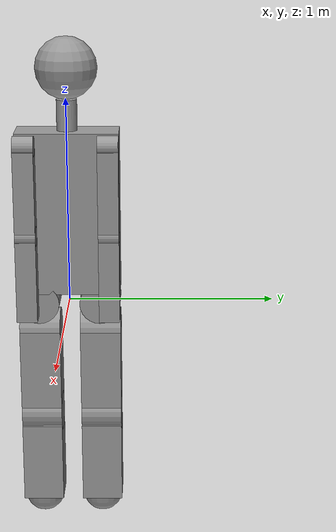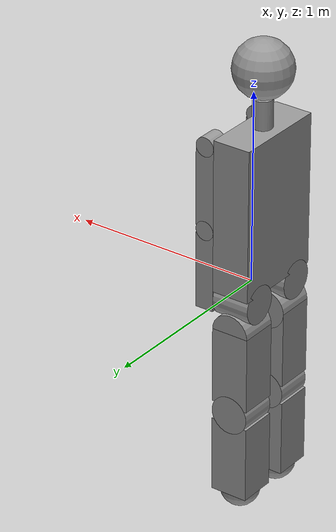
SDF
<?xml version='1.0'?>
<sdf version='1.6'>
  <model name='humanoid'>
    <link name='link_0_clone'>
      <pose frame=''>-0.052164 -0.150027 -0.86239 0 -0 0</pose>
      <inertial>
        <mass>1</mass>
        <inertia>
          <ixx>0.166667</ixx>
          <ixy>0</ixy>
          <ixz>0</ixz>
          <iyy>0.166667</iyy>
          <iyz>0</iyz>
          <izz>0.166667</izz>
        </inertia>
        <pose frame=''>0 0 0 0 -0 0</pose>
      </inertial>
      <self_collide>0</self_collide>
      <kinematic>0</kinematic>
      <visual name='visual'>
        <pose frame=''>0 0 0 0 -0 0</pose>
        <geometry>
          <box>
            <size>0.2 0.2 0.4</size>
          </box>
        </geometry>
        <material>
          <lighting>1</lighting>
          <script>
            <uri>file://media/materials/scripts/gazebo.material</uri>
            <name>Gazebo/Grey</name>
          </script>
          <shader type='pixel'>
            <normal_map>__default__</normal_map>
          </shader>
          <ambient>0.3 0.3 0.3 1</ambient>
          <diffuse>0.7 0.7 0.7 1</diffuse>
          <specular>0.01 0.01 0.01 1</specular>
          <emissive>0 0 0 1</emissive>
        </material>
        <transparency>0</transparency>
        <cast_shadows>1</cast_shadows>
      </visual>
      <collision name='collision'>
        <laser_retro>0</laser_retro>
        <max_contacts>10</max_contacts>
        <pose frame=''>0 0 0 0 -0 0</pose>
        <geometry>
          <box>
            <size>0.2 0.2 0.4</size>
          </box>
        </geometry>
        <surface>
          <friction>
            <ode>
              <mu>1</mu>
              <mu2>1</mu2>
              <fdir1>0 0 0</fdir1>
              <slip1>0</slip1>
              <slip2>0</slip2>
            </ode>
            <torsional>
              <coefficient>1</coefficient>
              <patch_radius>0</patch_radius>
              <surface_radius>0</surface_radius>
              <use_patch_radius>1</use_patch_radius>
              <ode>
                <slip>0</slip>
              </ode>
            </torsional>
          </friction>
          <bounce>
            <restitution_coefficient>0</restitution_coefficient>
            <threshold>1e+06</threshold>
          </bounce>
          <contact>
            <collide_without_contact>0</collide_without_contact>
            <collide_without_contact_bitmask>1</collide_without_contact_bitmask>
            <collide_bitmask>1</collide_bitmask>
            <ode>
              <soft_cfm>0</soft_cfm>
              <soft_erp>0.2</soft_erp>
              <kp>1e+13</kp>
              <kd>1</kd>
              <max_vel>0.01</max_vel>
              <min_depth>0</min_depth>
            </ode>
            <bullet>
              <split_impulse>1</split_impulse>
              <split_impulse_penetration_threshold>-0.01</split_impulse_penetration_threshold>
              <soft_cfm>0</soft_cfm>
              <soft_erp>0.2</soft_erp>
              <kp>1e+13</kp>
              <kd>1</kd>
            </bullet>
          </contact>
        </surface>
      </collision>
    </link>
    <link name='link_0_clone_clone'>
      <pose frame=''>-0.052164 0.149982 -0.86239 0 -0 0</pose>
      <inertial>
        <mass>1</mass>
        <inertia>
          <ixx>0.166667</ixx>
          <ixy>0</ixy>
          <ixz>0</ixz>
          <iyy>0.166667</iyy>
          <iyz>0</iyz>
          <izz>0.166667</izz>
        </inertia>
        <pose frame=''>0 0 0 0 -0 0</pose>
      </inertial>
      <self_collide>0</self_collide>
      <kinematic>0</kinematic>
      <visual name='visual'>
        <pose frame=''>0 0 0 0 -0 0</pose>
        <geometry>
          <box>
            <size>0.2 0.2 0.4</size>
          </box>
        </geometry>
        <material>
          <lighting>1</lighting>
          <script>
            <uri>file://media/materials/scripts/gazebo.material</uri>
            <name>Gazebo/Grey</name>
          </script>
          <shader type='pixel'>
            <normal_map>__default__</normal_map>
          </shader>
          <ambient>0.3 0.3 0.3 1</ambient>
          <diffuse>0.7 0.7 0.7 1</diffuse>
          <specular>0.01 0.01 0.01 1</specular>
          <emissive>0 0 0 1</emissive>
        </material>
        <transparency>0</transparency>
        <cast_shadows>1</cast_shadows>
      </visual>
      <collision name='collision'>
        <laser_retro>0</laser_retro>
        <max_contacts>10</max_contacts>
        <pose frame=''>0 0 0 0 -0 0</pose>
        <geometry>
          <box>
            <size>0.2 0.2 0.4</size>
          </box>
        </geometry>
        <surface>
          <friction>
            <ode>
              <mu>1</mu>
              <mu2>1</mu2>
              <fdir1>0 0 0</fdir1>
              <slip1>0</slip1>
              <slip2>0</slip2>
            </ode>
            <torsional>
              <coefficient>1</coefficient>
              <patch_radius>0</patch_radius>
              <surface_radius>0</surface_radius>
              <use_patch_radius>1</use_patch_radius>
              <ode>
                <slip>0</slip>
              </ode>
            </torsional>
          </friction>
          <bounce>
            <restitution_coefficient>0</restitution_coefficient>
            <threshold>1e+06</threshold>
          </bounce>
          <contact>
            <collide_without_contact>0</collide_without_contact>
            <collide_without_contact_bitmask>1</collide_without_contact_bitmask>
            <collide_bitmask>1</collide_bitmask>
            <ode>
              <soft_cfm>0</soft_cfm>
              <soft_erp>0.2</soft_erp>
              <kp>1e+13</kp>
              <kd>1</kd>
              <max_vel>0.01</max_vel>
              <min_depth>0</min_depth>
            </ode>
            <bullet>
              <split_impulse>1</split_impulse>
              <split_impulse_penetration_threshold>-0.01</split_impulse_penetration_threshold>
              <soft_cfm>0</soft_cfm>
              <soft_erp>0.2</soft_erp>
              <kp>1e+13</kp>
              <kd>1</kd>
            </bullet>
          </contact>
        </surface>
      </collision>
    </link>
    <link name='link_0_clone_clone_0'>
      <pose frame=''>-0.052164 -0.150003 -0.36239 0 -0 0</pose>
      <inertial>
        <mass>1</mass>
        <inertia>
          <ixx>0.166667</ixx>
          <ixy>0</ixy>
          <ixz>0</ixz>
          <iyy>0.166667</iyy>
          <iyz>0</iyz>
          <izz>0.166667</izz>
        </inertia>
        <pose frame=''>0 0 0 0 -0 0</pose>
      </inertial>
      <self_collide>0</self_collide>
      <kinematic>0</kinematic>
      <visual name='visual'>
        <pose frame=''>0 0 0 0 -0 0</pose>
        <geometry>
          <box>
            <size>0.2 0.2 0.4</size>
          </box>
        </geometry>
        <material>
          <lighting>1</lighting>
          <script>
            <uri>file://media/materials/scripts/gazebo.material</uri>
            <name>Gazebo/Grey</name>
          </script>
          <shader type='pixel'>
            <normal_map>__default__</normal_map>
          </shader>
          <ambient>0.3 0.3 0.3 1</ambient>
          <diffuse>0.7 0.7 0.7 1</diffuse>
          <specular>0.01 0.01 0.01 1</specular>
          <emissive>0 0 0 1</emissive>
        </material>
        <transparency>0</transparency>
        <cast_shadows>1</cast_shadows>
      </visual>
      <collision name='collision'>
        <laser_retro>0</laser_retro>
        <max_contacts>10</max_contacts>
        <pose frame=''>0 0 0 0 -0 0</pose>
        <geometry>
          <box>
            <size>0.2 0.2 0.4</size>
          </box>
        </geometry>
        <surface>
          <friction>
            <ode>
              <mu>1</mu>
              <mu2>1</mu2>
              <fdir1>0 0 0</fdir1>
              <slip1>0</slip1>
              <slip2>0</slip2>
            </ode>
            <torsional>
              <coefficient>1</coefficient>
              <patch_radius>0</patch_radius>
              <surface_radius>0</surface_radius>
              <use_patch_radius>1</use_patch_radius>
              <ode>
                <slip>0</slip>
              </ode>
            </torsional>
          </friction>
          <bounce>
            <restitution_coefficient>0</restitution_coefficient>
            <threshold>1e+06</threshold>
          </bounce>
          <contact>
            <collide_without_contact>0</collide_without_contact>
            <collide_without_contact_bitmask>1</collide_without_contact_bitmask>
            <collide_bitmask>1</collide_bitmask>
            <ode>
              <soft_cfm>0</soft_cfm>
              <soft_erp>0.2</soft_erp>
              <kp>1e+13</kp>
              <kd>1</kd>
              <max_vel>0.01</max_vel>
              <min_depth>0</min_depth>
            </ode>
            <bullet>
              <split_impulse>1</split_impulse>
              <split_impulse_penetration_threshold>-0.01</split_impulse_penetration_threshold>
              <soft_cfm>0</soft_cfm>
              <soft_erp>0.2</soft_erp>
              <kp>1e+13</kp>
              <kd>1</kd>
            </bullet>
          </contact>
        </surface>
      </collision>
    </link>
    <link name='link_0_clone_clone_0_clone'>
      <pose frame=''>0.097822 0.199959 0.127605 0 -0 0</pose>
      <inertial>
        <mass>1</mass>
        <inertia>
          <ixx>0.166667</ixx>
          <ixy>0</ixy>
          <ixz>0</ixz>
          <iyy>0.166667</iyy>
          <iyz>0</iyz>
          <izz>0.166667</izz>
        </inertia>
        <pose frame=''>0 0 0 0 -0 0</pose>
      </inertial>
      <self_collide>0</self_collide>
      <kinematic>0</kinematic>
      <gravity>1</gravity>
      <visual name='visual'>
        <pose frame=''>0 0 0 0 -0 0</pose>
        <geometry>
          <box>
            <size>0.1 0.1 0.4</size>
          </box>
        </geometry>
        <material>
          <lighting>1</lighting>
          <script>
            <uri>file://media/materials/scripts/gazebo.material</uri>
            <name>Gazebo/Grey</name>
          </script>
          <shader type='pixel'>
            <normal_map>__default__</normal_map>
          </shader>
          <ambient>0.3 0.3 0.3 1</ambient>
          <diffuse>0.7 0.7 0.7 1</diffuse>
          <specular>0.01 0.01 0.01 1</specular>
          <emissive>0 0 0 1</emissive>
        </material>
        <transparency>0</transparency>
        <cast_shadows>1</cast_shadows>
      </visual>
      <collision name='collision'>
        <laser_retro>0</laser_retro>
        <max_contacts>10</max_contacts>
        <pose frame=''>0 0 0 0 -0 0</pose>
        <geometry>
          <box>
            <size>0.1 0.1 0.4</size>
          </box>
        </geometry>
        <surface>
          <friction>
            <ode>
              <mu>1</mu>
              <mu2>1</mu2>
              <fdir1>0 0 0</fdir1>
              <slip1>0</slip1>
              <slip2>0</slip2>
            </ode>
            <torsional>
              <coefficient>1</coefficient>
              <patch_radius>0</patch_radius>
              <surface_radius>0</surface_radius>
              <use_patch_radius>1</use_patch_radius>
              <ode>
                <slip>0</slip>
              </ode>
            </torsional>
          </friction>
          <bounce>
            <restitution_coefficient>0</restitution_coefficient>
            <threshold>1e+06</threshold>
          </bounce>
          <contact>
            <collide_without_contact>0</collide_without_contact>
            <collide_without_contact_bitmask>1</collide_without_contact_bitmask>
            <collide_bitmask>1</collide_bitmask>
            <ode>
              <soft_cfm>0</soft_cfm>
              <soft_erp>0.2</soft_erp>
              <kp>1e+13</kp>
              <kd>1</kd>
              <max_vel>0.01</max_vel>
              <min_depth>0</min_depth>
            </ode>
            <bullet>
              <split_impulse>1</split_impulse>
              <split_impulse_penetration_threshold>-0.01</split_impulse_penetration_threshold>
              <soft_cfm>0</soft_cfm>
              <soft_erp>0.2</soft_erp>
              <kp>1e+13</kp>
              <kd>1</kd>
            </bullet>
          </contact>
        </surface>
      </collision>
    </link>
    <link name='link_0_clone_clone_0_clone_clone'>
      <pose frame=''>0.097822 -0.200031 0.127605 0 -0 0</pose>
      <inertial>
        <mass>1</mass>
        <inertia>
          <ixx>0.166667</ixx>
          <ixy>0</ixy>
          <ixz>0</ixz>
          <iyy>0.166667</iyy>
          <iyz>0</iyz>
          <izz>0.166667</izz>
        </inertia>
        <pose frame=''>0 0 0 0 -0 0</pose>
      </inertial>
      <self_collide>0</self_collide>
      <kinematic>0</kinematic>
      <visual name='visual'>
        <pose frame=''>0 0 0 0 -0 0</pose>
        <geometry>
          <box>
            <size>0.1 0.1 0.4</size>
          </box>
        </geometry>
        <material>
          <lighting>1</lighting>
          <script>
            <uri>file://media/materials/scripts/gazebo.material</uri>
            <name>Gazebo/Grey</name>
          </script>
          <shader type='pixel'>
            <normal_map>__default__</normal_map>
          </shader>
          <ambient>0.3 0.3 0.3 1</ambient>
          <diffuse>0.7 0.7 0.7 1</diffuse>
          <specular>0.01 0.01 0.01 1</specular>
          <emissive>0 0 0 1</emissive>
        </material>
        <transparency>0</transparency>
        <cast_shadows>1</cast_shadows>
      </visual>
      <collision name='collision'>
        <laser_retro>0</laser_retro>
        <max_contacts>10</max_contacts>
        <pose frame=''>0 0 0 0 -0 0</pose>
        <geometry>
          <box>
            <size>0.1 0.1 0.4</size>
          </box>
        </geometry>
        <surface>
          <friction>
            <ode>
              <mu>1</mu>
              <mu2>1</mu2>
              <fdir1>0 0 0</fdir1>
              <slip1>0</slip1>
              <slip2>0</slip2>
            </ode>
            <torsional>
              <coefficient>1</coefficient>
              <patch_radius>0</patch_radius>
              <surface_radius>0</surface_radius>
              <use_patch_radius>1</use_patch_radius>
              <ode>
                <slip>0</slip>
              </ode>
            </torsional>
          </friction>
          <bounce>
            <restitution_coefficient>0</restitution_coefficient>
            <threshold>1e+06</threshold>
          </bounce>
          <contact>
            <collide_without_contact>0</collide_without_contact>
            <collide_without_contact_bitmask>1</collide_without_contact_bitmask>
            <collide_bitmask>1</collide_bitmask>
            <ode>
              <soft_cfm>0</soft_cfm>
              <soft_erp>0.2</soft_erp>
              <kp>1e+13</kp>
              <kd>1</kd>
              <max_vel>0.01</max_vel>
              <min_depth>0</min_depth>
            </ode>
            <bullet>
              <split_impulse>1</split_impulse>
              <split_impulse_penetration_threshold>-0.01</split_impulse_penetration_threshold>
              <soft_cfm>0</soft_cfm>
              <soft_erp>0.2</soft_erp>
              <kp>1e+13</kp>
              <kd>1</kd>
            </bullet>
          </contact>
        </surface>
      </collision>
    </link>
    <link name='link_0_clone_clone_0_clone_clone_0'>
      <pose frame=''>0.097822 0.199981 0.567605 0 -0 0</pose>
      <inertial>
        <mass>1</mass>
        <inertia>
          <ixx>0.166667</ixx>
          <ixy>0</ixy>
          <ixz>0</ixz>
          <iyy>0.166667</iyy>
          <iyz>0</iyz>
          <izz>0.166667</izz>
        </inertia>
        <pose frame=''>0 0 0 0 -0 0</pose>
      </inertial>
      <self_collide>0</self_collide>
      <kinematic>0</kinematic>
      <visual name='visual'>
        <pose frame=''>0 0 0 0 -0 0</pose>
        <geometry>
          <box>
            <size>0.1 0.1 0.4</size>
          </box>
        </geometry>
        <material>
          <lighting>1</lighting>
          <script>
            <uri>file://media/materials/scripts/gazebo.material</uri>
            <name>Gazebo/Grey</name>
          </script>
          <shader type='pixel'>
            <normal_map>__default__</normal_map>
          </shader>
          <ambient>0.3 0.3 0.3 1</ambient>
          <diffuse>0.7 0.7 0.7 1</diffuse>
          <specular>0.01 0.01 0.01 1</specular>
          <emissive>0 0 0 1</emissive>
        </material>
        <transparency>0</transparency>
        <cast_shadows>1</cast_shadows>
      </visual>
      <collision name='collision'>
        <laser_retro>0</laser_retro>
        <max_contacts>10</max_contacts>
        <pose frame=''>0 0 0 0 -0 0</pose>
        <geometry>
          <box>
            <size>0.1 0.1 0.4</size>
          </box>
        </geometry>
        <surface>
          <friction>
            <ode>
              <mu>1</mu>
              <mu2>1</mu2>
              <fdir1>0 0 0</fdir1>
              <slip1>0</slip1>
              <slip2>0</slip2>
            </ode>
            <torsional>
              <coefficient>1</coefficient>
              <patch_radius>0</patch_radius>
              <surface_radius>0</surface_radius>
              <use_patch_radius>1</use_patch_radius>
              <ode>
                <slip>0</slip>
              </ode>
            </torsional>
          </friction>
          <bounce>
            <restitution_coefficient>0</restitution_coefficient>
            <threshold>1e+06</threshold>
          </bounce>
          <contact>
            <collide_without_contact>0</collide_without_contact>
            <collide_without_contact_bitmask>1</collide_without_contact_bitmask>
            <collide_bitmask>1</collide_bitmask>
            <ode>
              <soft_cfm>0</soft_cfm>
              <soft_erp>0.2</soft_erp>
              <kp>1e+13</kp>
              <kd>1</kd>
              <max_vel>0.01</max_vel>
              <min_depth>0</min_depth>
            </ode>
            <bullet>
              <split_impulse>1</split_impulse>
              <split_impulse_penetration_threshold>-0.01</split_impulse_penetration_threshold>
              <soft_cfm>0</soft_cfm>
              <soft_erp>0.2</soft_erp>
              <kp>1e+13</kp>
              <kd>1</kd>
            </bullet>
          </contact>
        </surface>
      </collision>
    </link>
    <link name='link_0_clone_clone_0_clone_clone_1'>
      <pose frame=''>0.097822 -0.20001 0.567605 0 -0 0</pose>
      <inertial>
        <mass>1</mass>
        <inertia>
          <ixx>0.166667</ixx>
          <ixy>0</ixy>
          <ixz>0</ixz>
          <iyy>0.166667</iyy>
          <iyz>0</iyz>
          <izz>0.166667</izz>
        </inertia>
        <pose frame=''>0 0 0 0 -0 0</pose>
      </inertial>
      <self_collide>0</self_collide>
      <kinematic>0</kinematic>
      <visual name='visual'>
        <pose frame=''>0 0 0 0 -0 0</pose>
        <geometry>
          <box>
            <size>0.1 0.1 0.4</size>
          </box>
        </geometry>
        <material>
          <lighting>1</lighting>
          <script>
            <uri>file://media/materials/scripts/gazebo.material</uri>
            <name>Gazebo/Grey</name>
          </script>
          <shader type='pixel'>
            <normal_map>__default__</normal_map>
          </shader>
          <ambient>0.3 0.3 0.3 1</ambient>
          <diffuse>0.7 0.7 0.7 1</diffuse>
          <specular>0.01 0.01 0.01 1</specular>
          <emissive>0 0 0 1</emissive>
        </material>
        <transparency>0</transparency>
        <cast_shadows>1</cast_shadows>
      </visual>
      <collision name='collision'>
        <laser_retro>0</laser_retro>
        <max_contacts>10</max_contacts>
        <pose frame=''>0 0 0 0 -0 0</pose>
        <geometry>
          <box>
            <size>0.1 0.1 0.4</size>
          </box>
        </geometry>
        <surface>
          <friction>
            <ode>
              <mu>1</mu>
              <mu2>1</mu2>
              <fdir1>0 0 0</fdir1>
              <slip1>0</slip1>
              <slip2>0</slip2>
            </ode>
            <torsional>
              <coefficient>1</coefficient>
              <patch_radius>0</patch_radius>
              <surface_radius>0</surface_radius>
              <use_patch_radius>1</use_patch_radius>
              <ode>
                <slip>0</slip>
              </ode>
            </torsional>
          </friction>
          <bounce>
            <restitution_coefficient>0</restitution_coefficient>
            <threshold>1e+06</threshold>
          </bounce>
          <contact>
            <collide_without_contact>0</collide_without_contact>
            <collide_without_contact_bitmask>1</collide_without_contact_bitmask>
            <collide_bitmask>1</collide_bitmask>
            <ode>
              <soft_cfm>0</soft_cfm>
              <soft_erp>0.2</soft_erp>
              <kp>1e+13</kp>
              <kd>1</kd>
              <max_vel>0.01</max_vel>
              <min_depth>0</min_depth>
            </ode>
            <bullet>
              <split_impulse>1</split_impulse>
              <split_impulse_penetration_threshold>-0.01</split_impulse_penetration_threshold>
              <soft_cfm>0</soft_cfm>
              <soft_erp>0.2</soft_erp>
              <kp>1e+13</kp>
              <kd>1</kd>
            </bullet>
          </contact>
        </surface>
      </collision>
    </link>
    <link name='link_0_clone_clone_1'>
      <pose frame=''>-0.052164 0.150006 -0.36239 0 -0 0</pose>
      <inertial>
        <mass>1</mass>
        <inertia>
          <ixx>0.166667</ixx>
          <ixy>0</ixy>
          <ixz>0</ixz>
          <iyy>0.166667</iyy>
          <iyz>0</iyz>
          <izz>0.166667</izz>
        </inertia>
        <pose frame=''>0 0 0 0 -0 0</pose>
      </inertial>
      <self_collide>0</self_collide>
      <kinematic>0</kinematic>
      <visual name='visual'>
        <pose frame=''>0 0 0 0 -0 0</pose>
        <geometry>
          <box>
            <size>0.2 0.2 0.4</size>
          </box>
        </geometry>
        <material>
          <lighting>1</lighting>
          <script>
            <uri>file://media/materials/scripts/gazebo.material</uri>
            <name>Gazebo/Grey</name>
          </script>
          <shader type='pixel'>
            <normal_map>__default__</normal_map>
          </shader>
          <ambient>0.3 0.3 0.3 1</ambient>
          <diffuse>0.7 0.7 0.7 1</diffuse>
          <specular>0.01 0.01 0.01 1</specular>
          <emissive>0 0 0 1</emissive>
        </material>
        <transparency>0</transparency>
        <cast_shadows>1</cast_shadows>
      </visual>
      <collision name='collision'>
        <laser_retro>0</laser_retro>
        <max_contacts>10</max_contacts>
        <pose frame=''>0 0 0 0 -0 0</pose>
        <geometry>
          <box>
            <size>0.2 0.2 0.4</size>
          </box>
        </geometry>
        <surface>
          <friction>
            <ode>
              <mu>1</mu>
              <mu2>1</mu2>
              <fdir1>0 0 0</fdir1>
              <slip1>0</slip1>
              <slip2>0</slip2>
            </ode>
            <torsional>
              <coefficient>1</coefficient>
              <patch_radius>0</patch_radius>
              <surface_radius>0</surface_radius>
              <use_patch_radius>1</use_patch_radius>
              <ode>
                <slip>0</slip>
              </ode>
            </torsional>
          </friction>
          <bounce>
            <restitution_coefficient>0</restitution_coefficient>
            <threshold>1e+06</threshold>
          </bounce>
          <contact>
            <collide_without_contact>0</collide_without_contact>
            <collide_without_contact_bitmask>1</collide_without_contact_bitmask>
            <collide_bitmask>1</collide_bitmask>
            <ode>
              <soft_cfm>0</soft_cfm>
              <soft_erp>0.2</soft_erp>
              <kp>1e+13</kp>
              <kd>1</kd>
              <max_vel>0.01</max_vel>
              <min_depth>0</min_depth>
            </ode>
            <bullet>
              <split_impulse>1</split_impulse>
              <split_impulse_penetration_threshold>-0.01</split_impulse_penetration_threshold>
              <soft_cfm>0</soft_cfm>
              <soft_erp>0.2</soft_erp>
              <kp>1e+13</kp>
              <kd>1</kd>
            </bullet>
          </contact>
        </surface>
      </collision>
    </link>
    <link name='link_1_clone'>
      <pose frame=''>-0.052164 -0.150027 -1.06239 0 -0 0</pose>
      <inertial>
        <mass>1</mass>
        <inertia>
          <ixx>0.1</ixx>
          <ixy>0</ixy>
          <ixz>0</ixz>
          <iyy>0.1</iyy>
          <iyz>0</iyz>
          <izz>0.1</izz>
        </inertia>
        <pose frame=''>0 0 0 0 -0 0</pose>
      </inertial>
      <self_collide>0</self_collide>
      <kinematic>0</kinematic>
      <gravity>1</gravity>
      <visual name='visual'>
        <pose frame=''>0 0 0 0 -0 0</pose>
        <geometry>
          <sphere>
            <radius>0.1</radius>
          </sphere>
        </geometry>
        <material>
          <lighting>1</lighting>
          <script>
            <uri>file://media/materials/scripts/gazebo.material</uri>
            <name>Gazebo/Grey</name>
          </script>
          <shader type='pixel'>
            <normal_map>__default__</normal_map>
          </shader>
          <ambient>0.3 0.3 0.3 1</ambient>
          <diffuse>0.7 0.7 0.7 1</diffuse>
          <specular>0.01 0.01 0.01 1</specular>
          <emissive>0 0 0 1</emissive>
        </material>
        <transparency>0</transparency>
        <cast_shadows>1</cast_shadows>
      </visual>
      <collision name='collision'>
        <laser_retro>0</laser_retro>
        <max_contacts>10</max_contacts>
        <pose frame=''>0 0 0 0 -0 0</pose>
        <geometry>
          <sphere>
            <radius>0.1</radius>
          </sphere>
        </geometry>
        <surface>
          <friction>
            <ode>
              <mu>1</mu>
              <mu2>1</mu2>
              <fdir1>0 0 0</fdir1>
              <slip1>0</slip1>
              <slip2>0</slip2>
            </ode>
            <torsional>
              <coefficient>1</coefficient>
              <patch_radius>0</patch_radius>
              <surface_radius>0</surface_radius>
              <use_patch_radius>1</use_patch_radius>
              <ode>
                <slip>0</slip>
              </ode>
            </torsional>
          </friction>
          <bounce>
            <restitution_coefficient>0</restitution_coefficient>
            <threshold>1e+06</threshold>
          </bounce>
          <contact>
            <collide_without_contact>0</collide_without_contact>
            <collide_without_contact_bitmask>1</collide_without_contact_bitmask>
            <collide_bitmask>1</collide_bitmask>
            <ode>
              <soft_cfm>0</soft_cfm>
              <soft_erp>0.2</soft_erp>
              <kp>1e+13</kp>
              <kd>1</kd>
              <max_vel>0.01</max_vel>
              <min_depth>0</min_depth>
            </ode>
            <bullet>
              <split_impulse>1</split_impulse>
              <split_impulse_penetration_threshold>-0.01</split_impulse_penetration_threshold>
              <soft_cfm>0</soft_cfm>
              <soft_erp>0.2</soft_erp>
              <kp>1e+13</kp>
              <kd>1</kd>
            </bullet>
          </contact>
        </surface>
      </collision>
    </link>
    <link name='link_1_clone_clone'>
      <pose frame=''>-0.052164 0.149982 -1.06239 0 -0 0</pose>
      <inertial>
        <mass>1</mass>
        <inertia>
          <ixx>0.1</ixx>
          <ixy>0</ixy>
          <ixz>0</ixz>
          <iyy>0.1</iyy>
          <iyz>0</iyz>
          <izz>0.1</izz>
        </inertia>
        <pose frame=''>0 0 0 0 -0 0</pose>
      </inertial>
      <self_collide>0</self_collide>
      <kinematic>0</kinematic>
      <gravity>1</gravity>
      <visual name='visual'>
        <pose frame=''>0 0 0 0 -0 0</pose>
        <geometry>
          <sphere>
            <radius>0.1</radius>
          </sphere>
        </geometry>
        <material>
          <lighting>1</lighting>
          <script>
            <uri>file://media/materials/scripts/gazebo.material</uri>
            <name>Gazebo/Grey</name>
          </script>
          <shader type='pixel'>
            <normal_map>__default__</normal_map>
          </shader>
          <ambient>0.3 0.3 0.3 1</ambient>
          <diffuse>0.7 0.7 0.7 1</diffuse>
          <specular>0.01 0.01 0.01 1</specular>
          <emissive>0 0 0 1</emissive>
        </material>
        <transparency>0</transparency>
        <cast_shadows>1</cast_shadows>
      </visual>
      <collision name='collision'>
        <laser_retro>0</laser_retro>
        <max_contacts>10</max_contacts>
        <pose frame=''>0 0 0 0 -0 0</pose>
        <geometry>
          <sphere>
            <radius>0.1</radius>
          </sphere>
        </geometry>
        <surface>
          <friction>
            <ode>
              <mu>1</mu>
              <mu2>1</mu2>
              <fdir1>0 0 0</fdir1>
              <slip1>0</slip1>
              <slip2>0</slip2>
            </ode>
            <torsional>
              <coefficient>1</coefficient>
              <patch_radius>0</patch_radius>
              <surface_radius>0</surface_radius>
              <use_patch_radius>1</use_patch_radius>
              <ode>
                <slip>0</slip>
              </ode>
            </torsional>
          </friction>
          <bounce>
            <restitution_coefficient>0</restitution_coefficient>
            <threshold>1e+06</threshold>
          </bounce>
          <contact>
            <collide_without_contact>0</collide_without_contact>
            <collide_without_contact_bitmask>1</collide_without_contact_bitmask>
            <collide_bitmask>1</collide_bitmask>
            <ode>
              <soft_cfm>0</soft_cfm>
              <soft_erp>0.2</soft_erp>
              <kp>1e+13</kp>
              <kd>1</kd>
              <max_vel>0.01</max_vel>
              <min_depth>0</min_depth>
            </ode>
            <bullet>
              <split_impulse>1</split_impulse>
              <split_impulse_penetration_threshold>-0.01</split_impulse_penetration_threshold>
              <soft_cfm>0</soft_cfm>
              <soft_erp>0.2</soft_erp>
              <kp>1e+13</kp>
              <kd>1</kd>
            </bullet>
          </contact>
        </surface>
      </collision>
    </link>
    <link name='link_1_clone_clone_clone'>
      <pose frame=''>-0.052178 7e-06 1.13761 0 -0 0</pose>
      <inertial>
        <mass>1</mass>
        <inertia>
          <ixx>0.1</ixx>
          <ixy>0</ixy>
          <ixz>0</ixz>
          <iyy>0.1</iyy>
          <iyz>0</iyz>
          <izz>0.1</izz>
        </inertia>
        <pose frame=''>0 0 0 0 -0 0</pose>
      </inertial>
      <self_collide>0</self_collide>
      <kinematic>0</kinematic>
      <gravity>1</gravity>
      <visual name='visual'>
        <pose frame=''>0 0 0 0 -0 0</pose>
        <geometry>
          <sphere>
            <radius>0.15</radius>
          </sphere>
        </geometry>
        <material>
          <lighting>1</lighting>
          <script>
            <uri>file://media/materials/scripts/gazebo.material</uri>
            <name>Gazebo/Grey</name>
          </script>
          <shader type='pixel'>
            <normal_map>__default__</normal_map>
          </shader>
          <ambient>0.3 0.3 0.3 1</ambient>
          <diffuse>0.7 0.7 0.7 1</diffuse>
          <specular>0.01 0.01 0.01 1</specular>
          <emissive>0 0 0 1</emissive>
        </material>
        <transparency>0</transparency>
        <cast_shadows>1</cast_shadows>
      </visual>
      <collision name='collision'>
        <laser_retro>0</laser_retro>
        <max_contacts>10</max_contacts>
        <pose frame=''>0 0 0 0 -0 0</pose>
        <geometry>
          <sphere>
            <radius>0.15</radius>
          </sphere>
        </geometry>
        <surface>
          <friction>
            <ode>
              <mu>1</mu>
              <mu2>1</mu2>
              <fdir1>0 0 0</fdir1>
              <slip1>0</slip1>
              <slip2>0</slip2>
            </ode>
            <torsional>
              <coefficient>1</coefficient>
              <patch_radius>0</patch_radius>
              <surface_radius>0</surface_radius>
              <use_patch_radius>1</use_patch_radius>
              <ode>
                <slip>0</slip>
              </ode>
            </torsional>
          </friction>
          <bounce>
            <restitution_coefficient>0</restitution_coefficient>
            <threshold>1e+06</threshold>
          </bounce>
          <contact>
            <collide_without_contact>0</collide_without_contact>
            <collide_without_contact_bitmask>1</collide_without_contact_bitmask>
            <collide_bitmask>1</collide_bitmask>
            <ode>
              <soft_cfm>0</soft_cfm>
              <soft_erp>0.2</soft_erp>
              <kp>1e+13</kp>
              <kd>1</kd>
              <max_vel>0.01</max_vel>
              <min_depth>0</min_depth>
            </ode>
            <bullet>
              <split_impulse>1</split_impulse>
              <split_impulse_penetration_threshold>-0.01</split_impulse_penetration_threshold>
              <soft_cfm>0</soft_cfm>
              <soft_erp>0.2</soft_erp>
              <kp>1e+13</kp>
              <kd>1</kd>
            </bullet>
          </contact>
        </surface>
      </collision>
    </link>
    <link name='link_2_clone'>
      <pose frame=''>-0.052164 -0.150003 -0.61239 1.5707 -0 0</pose>
      <inertial>
        <mass>1</mass>
        <inertia>
          <ixx>0.145833</ixx>
          <ixy>0</ixy>
          <ixz>0</ixz>
          <iyy>0.145833</iyy>
          <iyz>0</iyz>
          <izz>0.125</izz>
        </inertia>
        <pose frame=''>0 0 0 0 -0 0</pose>
      </inertial>
      <self_collide>0</self_collide>
      <kinematic>0</kinematic>
      <visual name='visual'>
        <pose frame=''>0 0 0 0 -0 0</pose>
        <geometry>
          <cylinder>
            <radius>0.1</radius>
            <length>0.2</length>
          </cylinder>
        </geometry>
        <material>
          <lighting>1</lighting>
          <script>
            <uri>file://media/materials/scripts/gazebo.material</uri>
            <name>Gazebo/Grey</name>
          </script>
          <shader type='pixel'>
            <normal_map>__default__</normal_map>
          </shader>
          <ambient>0.3 0.3 0.3 1</ambient>
          <diffuse>0.7 0.7 0.7 1</diffuse>
          <specular>0.01 0.01 0.01 1</specular>
          <emissive>0 0 0 1</emissive>
        </material>
        <transparency>0</transparency>
        <cast_shadows>1</cast_shadows>
      </visual>
      <collision name='collision'>
        <laser_retro>0</laser_retro>
        <max_contacts>10</max_contacts>
        <pose frame=''>0 0 0 0 -0 0</pose>
        <geometry>
          <cylinder>
            <radius>0.1</radius>
            <length>0.2</length>
          </cylinder>
        </geometry>
        <surface>
          <friction>
            <ode>
              <mu>1</mu>
              <mu2>1</mu2>
              <fdir1>0 0 0</fdir1>
              <slip1>0</slip1>
              <slip2>0</slip2>
            </ode>
            <torsional>
              <coefficient>1</coefficient>
              <patch_radius>0</patch_radius>
              <surface_radius>0</surface_radius>
              <use_patch_radius>1</use_patch_radius>
              <ode>
                <slip>0</slip>
              </ode>
            </torsional>
          </friction>
          <bounce>
            <restitution_coefficient>0</restitution_coefficient>
            <threshold>1e+06</threshold>
          </bounce>
          <contact>
            <collide_without_contact>0</collide_without_contact>
            <collide_without_contact_bitmask>1</collide_without_contact_bitmask>
            <collide_bitmask>1</collide_bitmask>
            <ode>
              <soft_cfm>0</soft_cfm>
              <soft_erp>0.2</soft_erp>
              <kp>1e+13</kp>
              <kd>1</kd>
              <max_vel>0.01</max_vel>
              <min_depth>0</min_depth>
            </ode>
            <bullet>
              <split_impulse>1</split_impulse>
              <split_impulse_penetration_threshold>-0.01</split_impulse_penetration_threshold>
              <soft_cfm>0</soft_cfm>
              <soft_erp>0.2</soft_erp>
              <kp>1e+13</kp>
              <kd>1</kd>
            </bullet>
          </contact>
        </surface>
      </collision>
    </link>
    <link name='link_2_clone_clone'>
      <pose frame=''>-0.052164 -0.149983 -0.16239 1.5707 -0 0</pose>
      <inertial>
        <mass>1</mass>
        <inertia>
          <ixx>0.145833</ixx>
          <ixy>0</ixy>
          <ixz>0</ixz>
          <iyy>0.145833</iyy>
          <iyz>0</iyz>
          <izz>0.125</izz>
        </inertia>
        <pose frame=''>0 0 0 0 -0 0</pose>
      </inertial>
      <self_collide>0</self_collide>
      <kinematic>0</kinematic>
      <visual name='visual'>
        <pose frame=''>0 0 0 0 -0 0</pose>
        <geometry>
          <cylinder>
            <radius>0.1</radius>
            <length>0.2</length>
          </cylinder>
        </geometry>
        <material>
          <lighting>1</lighting>
          <script>
            <uri>file://media/materials/scripts/gazebo.material</uri>
            <name>Gazebo/Grey</name>
          </script>
          <shader type='pixel'>
            <normal_map>__default__</normal_map>
          </shader>
          <ambient>0.3 0.3 0.3 1</ambient>
          <diffuse>0.7 0.7 0.7 1</diffuse>
          <specular>0.01 0.01 0.01 1</specular>
          <emissive>0 0 0 1</emissive>
        </material>
        <transparency>0</transparency>
        <cast_shadows>1</cast_shadows>
      </visual>
      <collision name='collision'>
        <laser_retro>0</laser_retro>
        <max_contacts>10</max_contacts>
        <pose frame=''>0 0 0 0 -0 0</pose>
        <geometry>
          <cylinder>
            <radius>0.1</radius>
            <length>0.2</length>
          </cylinder>
        </geometry>
        <surface>
          <friction>
            <ode>
              <mu>1</mu>
              <mu2>1</mu2>
              <fdir1>0 0 0</fdir1>
              <slip1>0</slip1>
              <slip2>0</slip2>
            </ode>
            <torsional>
              <coefficient>1</coefficient>
              <patch_radius>0</patch_radius>
              <surface_radius>0</surface_radius>
              <use_patch_radius>1</use_patch_radius>
              <ode>
                <slip>0</slip>
              </ode>
            </torsional>
          </friction>
          <bounce>
            <restitution_coefficient>0</restitution_coefficient>
            <threshold>1e+06</threshold>
          </bounce>
          <contact>
            <collide_without_contact>0</collide_without_contact>
            <collide_without_contact_bitmask>1</collide_without_contact_bitmask>
            <collide_bitmask>1</collide_bitmask>
            <ode>
              <soft_cfm>0</soft_cfm>
              <soft_erp>0.2</soft_erp>
              <kp>1e+13</kp>
              <kd>1</kd>
              <max_vel>0.01</max_vel>
              <min_depth>0</min_depth>
            </ode>
            <bullet>
              <split_impulse>1</split_impulse>
              <split_impulse_penetration_threshold>-0.01</split_impulse_penetration_threshold>
              <soft_cfm>0</soft_cfm>
              <soft_erp>0.2</soft_erp>
              <kp>1e+13</kp>
              <kd>1</kd>
            </bullet>
          </contact>
        </surface>
      </collision>
    </link>
    <link name='link_2_clone_clone_2'>
      <pose frame=''>0.097822 -0.20001 0.347605 1.5707 -0 0</pose>
      <inertial>
        <mass>1</mass>
        <inertia>
          <ixx>0.145833</ixx>
          <ixy>0</ixy>
          <ixz>0</ixz>
          <iyy>0.145833</iyy>
          <iyz>0</iyz>
          <izz>0.125</izz>
        </inertia>
        <pose frame=''>0 0 0 0 -0 0</pose>
      </inertial>
      <self_collide>0</self_collide>
      <kinematic>0</kinematic>
      <gravity>1</gravity>
      <visual name='visual'>
        <pose frame=''>0 0 0 0 -0 0</pose>
        <geometry>
          <cylinder>
            <radius>0.05</radius>
            <length>0.1</length>
          </cylinder>
        </geometry>
        <material>
          <lighting>1</lighting>
          <script>
            <uri>file://media/materials/scripts/gazebo.material</uri>
            <name>Gazebo/Grey</name>
          </script>
          <shader type='pixel'>
            <normal_map>__default__</normal_map>
          </shader>
          <ambient>0.3 0.3 0.3 1</ambient>
          <diffuse>0.7 0.7 0.7 1</diffuse>
          <specular>0.01 0.01 0.01 1</specular>
          <emissive>0 0 0 1</emissive>
        </material>
        <transparency>0</transparency>
        <cast_shadows>1</cast_shadows>
      </visual>
      <collision name='collision'>
        <laser_retro>0</laser_retro>
        <max_contacts>10</max_contacts>
        <pose frame=''>0 0 0 0 -0 0</pose>
        <geometry>
          <cylinder>
            <radius>0.05</radius>
            <length>0.1</length>
          </cylinder>
        </geometry>
        <surface>
          <friction>
            <ode>
              <mu>1</mu>
              <mu2>1</mu2>
              <fdir1>0 0 0</fdir1>
              <slip1>0</slip1>
              <slip2>0</slip2>
            </ode>
            <torsional>
              <coefficient>1</coefficient>
              <patch_radius>0</patch_radius>
              <surface_radius>0</surface_radius>
              <use_patch_radius>1</use_patch_radius>
              <ode>
                <slip>0</slip>
              </ode>
            </torsional>
          </friction>
          <bounce>
            <restitution_coefficient>0</restitution_coefficient>
            <threshold>1e+06</threshold>
          </bounce>
          <contact>
            <collide_without_contact>0</collide_without_contact>
            <collide_without_contact_bitmask>1</collide_without_contact_bitmask>
            <collide_bitmask>1</collide_bitmask>
            <ode>
              <soft_cfm>0</soft_cfm>
              <soft_erp>0.2</soft_erp>
              <kp>1e+13</kp>
              <kd>1</kd>
              <max_vel>0.01</max_vel>
              <min_depth>0</min_depth>
            </ode>
            <bullet>
              <split_impulse>1</split_impulse>
              <split_impulse_penetration_threshold>-0.01</split_impulse_penetration_threshold>
              <soft_cfm>0</soft_cfm>
              <soft_erp>0.2</soft_erp>
              <kp>1e+13</kp>
              <kd>1</kd>
            </bullet>
          </contact>
        </surface>
      </collision>
    </link>
    <link name='link_2_clone_clone_2_clone'>
      <pose frame=''>0.097822 0.199981 0.347605 1.5707 -0 0</pose>
      <inertial>
        <mass>1</mass>
        <inertia>
          <ixx>0.145833</ixx>
          <ixy>0</ixy>
          <ixz>0</ixz>
          <iyy>0.145833</iyy>
          <iyz>0</iyz>
          <izz>0.125</izz>
        </inertia>
        <pose frame=''>0 0 0 0 -0 0</pose>
      </inertial>
      <self_collide>0</self_collide>
      <kinematic>0</kinematic>
      <visual name='visual'>
        <pose frame=''>0 0 0 0 -0 0</pose>
        <geometry>
          <cylinder>
            <radius>0.05</radius>
            <length>0.1</length>
          </cylinder>
        </geometry>
        <material>
          <lighting>1</lighting>
          <script>
            <uri>file://media/materials/scripts/gazebo.material</uri>
            <name>Gazebo/Grey</name>
          </script>
          <shader type='pixel'>
            <normal_map>__default__</normal_map>
          </shader>
          <ambient>0.3 0.3 0.3 1</ambient>
          <diffuse>0.7 0.7 0.7 1</diffuse>
          <specular>0.01 0.01 0.01 1</specular>
          <emissive>0 0 0 1</emissive>
        </material>
        <transparency>0</transparency>
        <cast_shadows>1</cast_shadows>
      </visual>
      <collision name='collision'>
        <laser_retro>0</laser_retro>
        <max_contacts>10</max_contacts>
        <pose frame=''>0 0 0 0 -0 0</pose>
        <geometry>
          <cylinder>
            <radius>0.05</radius>
            <length>0.1</length>
          </cylinder>
        </geometry>
        <surface>
          <friction>
            <ode>
              <mu>1</mu>
              <mu2>1</mu2>
              <fdir1>0 0 0</fdir1>
              <slip1>0</slip1>
              <slip2>0</slip2>
            </ode>
            <torsional>
              <coefficient>1</coefficient>
              <patch_radius>0</patch_radius>
              <surface_radius>0</surface_radius>
              <use_patch_radius>1</use_patch_radius>
              <ode>
                <slip>0</slip>
              </ode>
            </torsional>
          </friction>
          <bounce>
            <restitution_coefficient>0</restitution_coefficient>
            <threshold>1e+06</threshold>
          </bounce>
          <contact>
            <collide_without_contact>0</collide_without_contact>
            <collide_without_contact_bitmask>1</collide_without_contact_bitmask>
            <collide_bitmask>1</collide_bitmask>
            <ode>
              <soft_cfm>0</soft_cfm>
              <soft_erp>0.2</soft_erp>
              <kp>1e+13</kp>
              <kd>1</kd>
              <max_vel>0.01</max_vel>
              <min_depth>0</min_depth>
            </ode>
            <bullet>
              <split_impulse>1</split_impulse>
              <split_impulse_penetration_threshold>-0.01</split_impulse_penetration_threshold>
              <soft_cfm>0</soft_cfm>
              <soft_erp>0.2</soft_erp>
              <kp>1e+13</kp>
              <kd>1</kd>
            </bullet>
          </contact>
        </surface>
      </collision>
    </link>
    <link name='link_2_clone_clone_2_clone_0'>
      <pose frame=''>0.097822 0.200002 0.787605 1.5707 -0 0</pose>
      <inertial>
        <mass>1</mass>
        <inertia>
          <ixx>0.145833</ixx>
          <ixy>0</ixy>
          <ixz>0</ixz>
          <iyy>0.145833</iyy>
          <iyz>0</iyz>
          <izz>0.125</izz>
        </inertia>
        <pose frame=''>0 0 0 0 -0 0</pose>
      </inertial>
      <self_collide>0</self_collide>
      <kinematic>0</kinematic>
      <visual name='visual'>
        <pose frame=''>0 0 0 0 -0 0</pose>
        <geometry>
          <cylinder>
            <radius>0.05</radius>
            <length>0.1</length>
          </cylinder>
        </geometry>
        <material>
          <lighting>1</lighting>
          <script>
            <uri>file://media/materials/scripts/gazebo.material</uri>
            <name>Gazebo/Grey</name>
          </script>
          <shader type='pixel'>
            <normal_map>__default__</normal_map>
          </shader>
          <ambient>0.3 0.3 0.3 1</ambient>
          <diffuse>0.7 0.7 0.7 1</diffuse>
          <specular>0.01 0.01 0.01 1</specular>
          <emissive>0 0 0 1</emissive>
        </material>
        <transparency>0</transparency>
        <cast_shadows>1</cast_shadows>
      </visual>
      <collision name='collision'>
        <laser_retro>0</laser_retro>
        <max_contacts>10</max_contacts>
        <pose frame=''>0 0 0 0 -0 0</pose>
        <geometry>
          <cylinder>
            <radius>0.05</radius>
            <length>0.1</length>
          </cylinder>
        </geometry>
        <surface>
          <friction>
            <ode>
              <mu>1</mu>
              <mu2>1</mu2>
              <fdir1>0 0 0</fdir1>
              <slip1>0</slip1>
              <slip2>0</slip2>
            </ode>
            <torsional>
              <coefficient>1</coefficient>
              <patch_radius>0</patch_radius>
              <surface_radius>0</surface_radius>
              <use_patch_radius>1</use_patch_radius>
              <ode>
                <slip>0</slip>
              </ode>
            </torsional>
          </friction>
          <bounce>
            <restitution_coefficient>0</restitution_coefficient>
            <threshold>1e+06</threshold>
          </bounce>
          <contact>
            <collide_without_contact>0</collide_without_contact>
            <collide_without_contact_bitmask>1</collide_without_contact_bitmask>
            <collide_bitmask>1</collide_bitmask>
            <ode>
              <soft_cfm>0</soft_cfm>
              <soft_erp>0.2</soft_erp>
              <kp>1e+13</kp>
              <kd>1</kd>
              <max_vel>0.01</max_vel>
              <min_depth>0</min_depth>
            </ode>
            <bullet>
              <split_impulse>1</split_impulse>
              <split_impulse_penetration_threshold>-0.01</split_impulse_penetration_threshold>
              <soft_cfm>0</soft_cfm>
              <soft_erp>0.2</soft_erp>
              <kp>1e+13</kp>
              <kd>1</kd>
            </bullet>
          </contact>
        </surface>
      </collision>
    </link>
    <link name='link_2_clone_clone_2_clone_1'>
      <pose frame=''>0.097822 -0.199989 0.787605 1.5707 -0 0</pose>
      <inertial>
        <mass>1</mass>
        <inertia>
          <ixx>0.145833</ixx>
          <ixy>0</ixy>
          <ixz>0</ixz>
          <iyy>0.145833</iyy>
          <iyz>0</iyz>
          <izz>0.125</izz>
        </inertia>
        <pose frame=''>0 0 0 0 -0 0</pose>
      </inertial>
      <self_collide>0</self_collide>
      <kinematic>0</kinematic>
      <visual name='visual'>
        <pose frame=''>0 0 0 0 -0 0</pose>
        <geometry>
          <cylinder>
            <radius>0.05</radius>
            <length>0.1</length>
          </cylinder>
        </geometry>
        <material>
          <lighting>1</lighting>
          <script>
            <uri>file://media/materials/scripts/gazebo.material</uri>
            <name>Gazebo/Grey</name>
          </script>
          <shader type='pixel'>
            <normal_map>__default__</normal_map>
          </shader>
          <ambient>0.3 0.3 0.3 1</ambient>
          <diffuse>0.7 0.7 0.7 1</diffuse>
          <specular>0.01 0.01 0.01 1</specular>
          <emissive>0 0 0 1</emissive>
        </material>
        <transparency>0</transparency>
        <cast_shadows>1</cast_shadows>
      </visual>
      <collision name='collision'>
        <laser_retro>0</laser_retro>
        <max_contacts>10</max_contacts>
        <pose frame=''>0 0 0 0 -0 0</pose>
        <geometry>
          <cylinder>
            <radius>0.05</radius>
            <length>0.1</length>
          </cylinder>
        </geometry>
        <surface>
          <friction>
            <ode>
              <mu>1</mu>
              <mu2>1</mu2>
              <fdir1>0 0 0</fdir1>
              <slip1>0</slip1>
              <slip2>0</slip2>
            </ode>
            <torsional>
              <coefficient>1</coefficient>
              <patch_radius>0</patch_radius>
              <surface_radius>0</surface_radius>
              <use_patch_radius>1</use_patch_radius>
              <ode>
                <slip>0</slip>
              </ode>
            </torsional>
          </friction>
          <bounce>
            <restitution_coefficient>0</restitution_coefficient>
            <threshold>1e+06</threshold>
          </bounce>
          <contact>
            <collide_without_contact>0</collide_without_contact>
            <collide_without_contact_bitmask>1</collide_without_contact_bitmask>
            <collide_bitmask>1</collide_bitmask>
            <ode>
              <soft_cfm>0</soft_cfm>
              <soft_erp>0.2</soft_erp>
              <kp>1e+13</kp>
              <kd>1</kd>
              <max_vel>0.01</max_vel>
              <min_depth>0</min_depth>
            </ode>
            <bullet>
              <split_impulse>1</split_impulse>
              <split_impulse_penetration_threshold>-0.01</split_impulse_penetration_threshold>
              <soft_cfm>0</soft_cfm>
              <soft_erp>0.2</soft_erp>
              <kp>1e+13</kp>
              <kd>1</kd>
            </bullet>
          </contact>
        </surface>
      </collision>
    </link>
    <link name='link_2_clone_clone_2_clone_1_clone'>
      <pose frame=''>-0.052178 7e-06 0.91261 0 -0 0</pose>
      <inertial>
        <mass>1</mass>
        <inertia>
          <ixx>0.145833</ixx>
          <ixy>0</ixy>
          <ixz>0</ixz>
          <iyy>0.145833</iyy>
          <iyz>0</iyz>
          <izz>0.125</izz>
        </inertia>
        <pose frame=''>0 0 0 0 -0 0</pose>
      </inertial>
      <self_collide>0</self_collide>
      <kinematic>0</kinematic>
      <gravity>1</gravity>
      <visual name='visual'>
        <pose frame=''>0 0 0 0 -0 0</pose>
        <geometry>
          <cylinder>
            <radius>0.05</radius>
            <length>0.15</length>
          </cylinder>
        </geometry>
        <material>
          <lighting>1</lighting>
          <script>
            <uri>file://media/materials/scripts/gazebo.material</uri>
            <name>Gazebo/Grey</name>
          </script>
          <shader type='pixel'>
            <normal_map>__default__</normal_map>
          </shader>
          <ambient>0.3 0.3 0.3 1</ambient>
          <diffuse>0.7 0.7 0.7 1</diffuse>
          <specular>0.01 0.01 0.01 1</specular>
          <emissive>0 0 0 1</emissive>
        </material>
        <transparency>0</transparency>
        <cast_shadows>1</cast_shadows>
      </visual>
      <collision name='collision'>
        <laser_retro>0</laser_retro>
        <max_contacts>10</max_contacts>
        <pose frame=''>0 0 0 0 -0 0</pose>
        <geometry>
          <cylinder>
            <radius>0.05</radius>
            <length>0.15</length>
          </cylinder>
        </geometry>
        <surface>
          <friction>
            <ode>
              <mu>1</mu>
              <mu2>1</mu2>
              <fdir1>0 0 0</fdir1>
              <slip1>0</slip1>
              <slip2>0</slip2>
            </ode>
            <torsional>
              <coefficient>1</coefficient>
              <patch_radius>0</patch_radius>
              <surface_radius>0</surface_radius>
              <use_patch_radius>1</use_patch_radius>
              <ode>
                <slip>0</slip>
              </ode>
            </torsional>
          </friction>
          <bounce>
            <restitution_coefficient>0</restitution_coefficient>
            <threshold>1e+06</threshold>
          </bounce>
          <contact>
            <collide_without_contact>0</collide_without_contact>
            <collide_without_contact_bitmask>1</collide_without_contact_bitmask>
            <collide_bitmask>1</collide_bitmask>
            <ode>
              <soft_cfm>0</soft_cfm>
              <soft_erp>0.2</soft_erp>
              <kp>1e+13</kp>
              <kd>1</kd>
              <max_vel>0.01</max_vel>
              <min_depth>0</min_depth>
            </ode>
            <bullet>
              <split_impulse>1</split_impulse>
              <split_impulse_penetration_threshold>-0.01</split_impulse_penetration_threshold>
              <soft_cfm>0</soft_cfm>
              <soft_erp>0.2</soft_erp>
              <kp>1e+13</kp>
              <kd>1</kd>
            </bullet>
          </contact>
        </surface>
      </collision>
    </link>
    <link name='link_2_clone_clone_clone'>
      <pose frame=''>-0.052164 0.149997 -0.16239 1.5707 -0 0</pose>
      <inertial>
        <mass>1</mass>
        <inertia>
          <ixx>0.145833</ixx>
          <ixy>0</ixy>
          <ixz>0</ixz>
          <iyy>0.145833</iyy>
          <iyz>0</iyz>
          <izz>0.125</izz>
        </inertia>
        <pose frame=''>0 0 0 0 -0 0</pose>
      </inertial>
      <self_collide>0</self_collide>
      <kinematic>0</kinematic>
      <visual name='visual'>
        <pose frame=''>0 0 0 0 -0 0</pose>
        <geometry>
          <cylinder>
            <radius>0.1</radius>
            <length>0.2</length>
          </cylinder>
        </geometry>
        <material>
          <lighting>1</lighting>
          <script>
            <uri>file://media/materials/scripts/gazebo.material</uri>
            <name>Gazebo/Grey</name>
          </script>
          <shader type='pixel'>
            <normal_map>__default__</normal_map>
          </shader>
          <ambient>0.3 0.3 0.3 1</ambient>
          <diffuse>0.7 0.7 0.7 1</diffuse>
          <specular>0.01 0.01 0.01 1</specular>
          <emissive>0 0 0 1</emissive>
        </material>
        <transparency>0</transparency>
        <cast_shadows>1</cast_shadows>
      </visual>
      <collision name='collision'>
        <laser_retro>0</laser_retro>
        <max_contacts>10</max_contacts>
        <pose frame=''>0 0 0 0 -0 0</pose>
        <geometry>
          <cylinder>
            <radius>0.1</radius>
            <length>0.2</length>
          </cylinder>
        </geometry>
        <surface>
          <friction>
            <ode>
              <mu>1</mu>
              <mu2>1</mu2>
              <fdir1>0 0 0</fdir1>
              <slip1>0</slip1>
              <slip2>0</slip2>
            </ode>
            <torsional>
              <coefficient>1</coefficient>
              <patch_radius>0</patch_radius>
              <surface_radius>0</surface_radius>
              <use_patch_radius>1</use_patch_radius>
              <ode>
                <slip>0</slip>
              </ode>
            </torsional>
          </friction>
          <bounce>
            <restitution_coefficient>0</restitution_coefficient>
            <threshold>1e+06</threshold>
          </bounce>
          <contact>
            <collide_without_contact>0</collide_without_contact>
            <collide_without_contact_bitmask>1</collide_without_contact_bitmask>
            <collide_bitmask>1</collide_bitmask>
            <ode>
              <soft_cfm>0</soft_cfm>
              <soft_erp>0.2</soft_erp>
              <kp>1e+13</kp>
              <kd>1</kd>
              <max_vel>0.01</max_vel>
              <min_depth>0</min_depth>
            </ode>
            <bullet>
              <split_impulse>1</split_impulse>
              <split_impulse_penetration_threshold>-0.01</split_impulse_penetration_threshold>
              <soft_cfm>0</soft_cfm>
              <soft_erp>0.2</soft_erp>
              <kp>1e+13</kp>
              <kd>1</kd>
            </bullet>
          </contact>
        </surface>
      </collision>
    </link>
    <link name='link_2_clone_clone_clone_clone'>
      <pose frame=''>-0.052164 0.150006 -0.61239 1.5707 -0 0</pose>
      <inertial>
        <mass>1</mass>
        <inertia>
          <ixx>0.145833</ixx>
          <ixy>0</ixy>
          <ixz>0</ixz>
          <iyy>0.145833</iyy>
          <iyz>0</iyz>
          <izz>0.125</izz>
        </inertia>
        <pose frame=''>0 0 0 0 -0 0</pose>
      </inertial>
      <self_collide>0</self_collide>
      <kinematic>0</kinematic>
      <visual name='visual'>
        <pose frame=''>0 0 0 0 -0 0</pose>
        <geometry>
          <cylinder>
            <radius>0.1</radius>
            <length>0.2</length>
          </cylinder>
        </geometry>
        <material>
          <lighting>1</lighting>
          <script>
            <uri>file://media/materials/scripts/gazebo.material</uri>
            <name>Gazebo/Grey</name>
          </script>
          <shader type='pixel'>
            <normal_map>__default__</normal_map>
          </shader>
          <ambient>0.3 0.3 0.3 1</ambient>
          <diffuse>0.7 0.7 0.7 1</diffuse>
          <specular>0.01 0.01 0.01 1</specular>
          <emissive>0 0 0 1</emissive>
        </material>
        <transparency>0</transparency>
        <cast_shadows>1</cast_shadows>
      </visual>
      <collision name='collision'>
        <laser_retro>0</laser_retro>
        <max_contacts>10</max_contacts>
        <pose frame=''>0 0 0 0 -0 0</pose>
        <geometry>
          <cylinder>
            <radius>0.1</radius>
            <length>0.2</length>
          </cylinder>
        </geometry>
        <surface>
          <friction>
            <ode>
              <mu>1</mu>
              <mu2>1</mu2>
              <fdir1>0 0 0</fdir1>
              <slip1>0</slip1>
              <slip2>0</slip2>
            </ode>
            <torsional>
              <coefficient>1</coefficient>
              <patch_radius>0</patch_radius>
              <surface_radius>0</surface_radius>
              <use_patch_radius>1</use_patch_radius>
              <ode>
                <slip>0</slip>
              </ode>
            </torsional>
          </friction>
          <bounce>
            <restitution_coefficient>0</restitution_coefficient>
            <threshold>1e+06</threshold>
          </bounce>
          <contact>
            <collide_without_contact>0</collide_without_contact>
            <collide_without_contact_bitmask>1</collide_without_contact_bitmask>
            <collide_bitmask>1</collide_bitmask>
            <ode>
              <soft_cfm>0</soft_cfm>
              <soft_erp>0.2</soft_erp>
              <kp>1e+13</kp>
              <kd>1</kd>
              <max_vel>0.01</max_vel>
              <min_depth>0</min_depth>
            </ode>
            <bullet>
              <split_impulse>1</split_impulse>
              <split_impulse_penetration_threshold>-0.01</split_impulse_penetration_threshold>
              <soft_cfm>0</soft_cfm>
              <soft_erp>0.2</soft_erp>
              <kp>1e+13</kp>
              <kd>1</kd>
            </bullet>
          </contact>
        </surface>
      </collision>
    </link>
    <link name='link_2_clone_clone_clone_clone_0'>
      <pose frame=''>-0.052178 -0.149983 -0.01239 1.5707 0 1.5707</pose>
      <inertial>
        <mass>1</mass>
        <inertia>
          <ixx>0.145833</ixx>
          <ixy>0</ixy>
          <ixz>0</ixz>
          <iyy>0.145833</iyy>
          <iyz>0</iyz>
          <izz>0.125</izz>
        </inertia>
        <pose frame=''>0 0 0 0 -0 0</pose>
      </inertial>
      <self_collide>0</self_collide>
      <kinematic>0</kinematic>
      <gravity>1</gravity>
      <visual name='visual'>
        <pose frame=''>0 0 0 0 -0 0</pose>
        <geometry>
          <cylinder>
            <radius>0.1</radius>
            <length>0.2</length>
          </cylinder>
        </geometry>
        <material>
          <lighting>1</lighting>
          <script>
            <uri>file://media/materials/scripts/gazebo.material</uri>
            <name>Gazebo/Grey</name>
          </script>
          <shader type='pixel'>
            <normal_map>__default__</normal_map>
          </shader>
          <ambient>0.3 0.3 0.3 1</ambient>
          <diffuse>0.7 0.7 0.7 1</diffuse>
          <specular>0.01 0.01 0.01 1</specular>
          <emissive>0 0 0 1</emissive>
        </material>
        <transparency>0</transparency>
        <cast_shadows>1</cast_shadows>
      </visual>
      <collision name='collision'>
        <laser_retro>0</laser_retro>
        <max_contacts>10</max_contacts>
        <pose frame=''>0 0 0 0 -0 0</pose>
        <geometry>
          <cylinder>
            <radius>0.1</radius>
            <length>0.2</length>
          </cylinder>
        </geometry>
        <surface>
          <friction>
            <ode>
              <mu>1</mu>
              <mu2>1</mu2>
              <fdir1>0 0 0</fdir1>
              <slip1>0</slip1>
              <slip2>0</slip2>
            </ode>
            <torsional>
              <coefficient>1</coefficient>
              <patch_radius>0</patch_radius>
              <surface_radius>0</surface_radius>
              <use_patch_radius>1</use_patch_radius>
              <ode>
                <slip>0</slip>
              </ode>
            </torsional>
          </friction>
          <bounce>
            <restitution_coefficient>0</restitution_coefficient>
            <threshold>1e+06</threshold>
          </bounce>
          <contact>
            <collide_without_contact>0</collide_without_contact>
            <collide_without_contact_bitmask>1</collide_without_contact_bitmask>
            <collide_bitmask>1</collide_bitmask>
            <ode>
              <soft_cfm>0</soft_cfm>
              <soft_erp>0.2</soft_erp>
              <kp>1e+13</kp>
              <kd>1</kd>
              <max_vel>0.01</max_vel>
              <min_depth>0</min_depth>
            </ode>
            <bullet>
              <split_impulse>1</split_impulse>
              <split_impulse_penetration_threshold>-0.01</split_impulse_penetration_threshold>
              <soft_cfm>0</soft_cfm>
              <soft_erp>0.2</soft_erp>
              <kp>1e+13</kp>
              <kd>1</kd>
            </bullet>
          </contact>
        </surface>
      </collision>
    </link>
    <link name='link_2_clone_clone_clone_clone_0_clone'>
      <pose frame=''>-0.052178 0.149997 -0.01239 1.5707 0 1.5707</pose>
      <inertial>
        <mass>1</mass>
        <inertia>
          <ixx>0.145833</ixx>
          <ixy>0</ixy>
          <ixz>0</ixz>
          <iyy>0.145833</iyy>
          <iyz>0</iyz>
          <izz>0.125</izz>
        </inertia>
        <pose frame=''>0 0 0 0 -0 0</pose>
      </inertial>
      <self_collide>0</self_collide>
      <kinematic>0</kinematic>
      <visual name='visual'>
        <pose frame=''>0 0 0 0 -0 0</pose>
        <geometry>
          <cylinder>
            <radius>0.1</radius>
            <length>0.2</length>
          </cylinder>
        </geometry>
        <material>
          <lighting>1</lighting>
          <script>
            <uri>file://media/materials/scripts/gazebo.material</uri>
            <name>Gazebo/Grey</name>
          </script>
          <shader type='pixel'>
            <normal_map>__default__</normal_map>
          </shader>
          <ambient>0.3 0.3 0.3 1</ambient>
          <diffuse>0.7 0.7 0.7 1</diffuse>
          <specular>0.01 0.01 0.01 1</specular>
          <emissive>0 0 0 1</emissive>
        </material>
        <transparency>0</transparency>
        <cast_shadows>1</cast_shadows>
      </visual>
      <collision name='collision'>
        <laser_retro>0</laser_retro>
        <max_contacts>10</max_contacts>
        <pose frame=''>0 0 0 0 -0 0</pose>
        <geometry>
          <cylinder>
            <radius>0.1</radius>
            <length>0.2</length>
          </cylinder>
        </geometry>
        <surface>
          <friction>
            <ode>
              <mu>1</mu>
              <mu2>1</mu2>
              <fdir1>0 0 0</fdir1>
              <slip1>0</slip1>
              <slip2>0</slip2>
            </ode>
            <torsional>
              <coefficient>1</coefficient>
              <patch_radius>0</patch_radius>
              <surface_radius>0</surface_radius>
              <use_patch_radius>1</use_patch_radius>
              <ode>
                <slip>0</slip>
              </ode>
            </torsional>
          </friction>
          <bounce>
            <restitution_coefficient>0</restitution_coefficient>
            <threshold>1e+06</threshold>
          </bounce>
          <contact>
            <collide_without_contact>0</collide_without_contact>
            <collide_without_contact_bitmask>1</collide_without_contact_bitmask>
            <collide_bitmask>1</collide_bitmask>
            <ode>
              <soft_cfm>0</soft_cfm>
              <soft_erp>0.2</soft_erp>
              <kp>1e+13</kp>
              <kd>1</kd>
              <max_vel>0.01</max_vel>
              <min_depth>0</min_depth>
            </ode>
            <bullet>
              <split_impulse>1</split_impulse>
              <split_impulse_penetration_threshold>-0.01</split_impulse_penetration_threshold>
              <soft_cfm>0</soft_cfm>
              <soft_erp>0.2</soft_erp>
              <kp>1e+13</kp>
              <kd>1</kd>
            </bullet>
          </contact>
        </surface>
      </collision>
    </link>
    <link name='link_4_clone'>
      <pose frame=''>-0.052178 7e-06 0.43761 0 -0 0</pose>
      <inertial>
        <mass>1</mass>
        <inertia>
          <ixx>0.166667</ixx>
          <ixy>0</ixy>
          <ixz>0</ixz>
          <iyy>0.166667</iyy>
          <iyz>0</iyz>
          <izz>0.166667</izz>
        </inertia>
        <pose frame=''>0 0 0 0 -0 0</pose>
      </inertial>
      <self_collide>0</self_collide>
      <kinematic>0</kinematic>
      <visual name='visual'>
        <pose frame=''>0 0 0 0 -0 0</pose>
        <geometry>
          <box>
            <size>0.2 0.5 0.8</size>
          </box>
        </geometry>
        <material>
          <lighting>1</lighting>
          <script>
            <uri>file://media/materials/scripts/gazebo.material</uri>
            <name>Gazebo/Grey</name>
          </script>
          <shader type='pixel'>
            <normal_map>__default__</normal_map>
          </shader>
          <ambient>0.3 0.3 0.3 1</ambient>
          <diffuse>0.7 0.7 0.7 1</diffuse>
          <specular>0.01 0.01 0.01 1</specular>
          <emissive>0 0 0 1</emissive>
        </material>
        <transparency>0</transparency>
        <cast_shadows>1</cast_shadows>
      </visual>
      <collision name='collision'>
        <laser_retro>0</laser_retro>
        <max_contacts>10</max_contacts>
        <pose frame=''>0 0 0 0 -0 0</pose>
        <geometry>
          <box>
            <size>0.2 0.5 0.8</size>
          </box>
        </geometry>
        <surface>
          <friction>
            <ode>
              <mu>1</mu>
              <mu2>1</mu2>
              <fdir1>0 0 0</fdir1>
              <slip1>0</slip1>
              <slip2>0</slip2>
            </ode>
            <torsional>
              <coefficient>1</coefficient>
              <patch_radius>0</patch_radius>
              <surface_radius>0</surface_radius>
              <use_patch_radius>1</use_patch_radius>
              <ode>
                <slip>0</slip>
              </ode>
            </torsional>
          </friction>
          <bounce>
            <restitution_coefficient>0</restitution_coefficient>
            <threshold>1e+06</threshold>
          </bounce>
          <contact>
            <collide_without_contact>0</collide_without_contact>
            <collide_without_contact_bitmask>1</collide_without_contact_bitmask>
            <collide_bitmask>1</collide_bitmask>
            <ode>
              <soft_cfm>0</soft_cfm>
              <soft_erp>0.2</soft_erp>
              <kp>1e+13</kp>
              <kd>1</kd>
              <max_vel>0.01</max_vel>
              <min_depth>0</min_depth>
            </ode>
            <bullet>
              <split_impulse>1</split_impulse>
              <split_impulse_penetration_threshold>-0.01</split_impulse_penetration_threshold>
              <soft_cfm>0</soft_cfm>
              <soft_erp>0.2</soft_erp>
              <kp>1e+13</kp>
              <kd>1</kd>
            </bullet>
          </contact>
        </surface>
      </collision>
    </link>
    <joint name='link_0_clone_JOINT_28' type='fixed'>
      <parent>link_0_clone</parent>
      <child>link_1_clone</child>
      <pose frame=''>0 0 0 0 -0 0</pose>
      <physics>
        <ode>
          <limit>
            <cfm>0</cfm>
            <erp>0.2</erp>
          </limit>
          <suspension>
            <cfm>0</cfm>
            <erp>0.2</erp>
          </suspension>
        </ode>
      </physics>
    </joint>
    <joint name='link_0_clone_clone_0_JOINT_24' type='revolute'>
      <parent>link_0_clone_clone_0</parent>
      <child>link_2_clone</child>
      <pose frame=''>0 0 0 0 -0 0</pose>
      <axis>
        <xyz>0 0 1</xyz>
        <use_parent_model_frame>0</use_parent_model_frame>
        <limit>
          <lower>-1.5707</lower>
          <upper>0.1</upper>
          <effort>-1</effort>
          <velocity>-1</velocity>
        </limit>
        <dynamics>
          <spring_reference>0</spring_reference>
          <spring_stiffness>0</spring_stiffness>
          <damping>0</damping>
          <friction>0</friction>
        </dynamics>
      </axis>
      <physics>
        <ode>
          <limit>
            <cfm>0</cfm>
            <erp>0.2</erp>
          </limit>
          <suspension>
            <cfm>0</cfm>
            <erp>0.2</erp>
          </suspension>
        </ode>
      </physics>
    </joint>
    <joint name='link_0_clone_clone_0_clone_clone_0_JOINT_13' type='revolute'>
      <parent>link_0_clone_clone_0_clone_clone_0</parent>
      <child>link_2_clone_clone_2_clone</child>
      <pose frame=''>0 0 0 0 -0 0</pose>
      <axis>
        <xyz>0 0 1</xyz>
        <use_parent_model_frame>0</use_parent_model_frame>
        <limit>
          <lower>0.1</lower>
          <upper>1.5707</upper>
          <effort>-1</effort>
          <velocity>-1</velocity>
        </limit>
        <dynamics>
          <spring_reference>0</spring_reference>
          <spring_stiffness>0</spring_stiffness>
          <damping>0</damping>
          <friction>0</friction>
        </dynamics>
      </axis>
      <physics>
        <ode>
          <limit>
            <cfm>0</cfm>
            <erp>0.2</erp>
          </limit>
          <suspension>
            <cfm>0</cfm>
            <erp>0.2</erp>
          </suspension>
        </ode>
      </physics>
    </joint>
    <joint name='link_0_clone_clone_0_clone_clone_1_JOINT_14' type='revolute'>
      <parent>link_0_clone_clone_0_clone_clone_1</parent>
      <child>link_2_clone_clone_2</child>
      <pose frame=''>0 0 0 0 -0 0</pose>
      <axis>
        <xyz>0 0 1</xyz>
        <use_parent_model_frame>0</use_parent_model_frame>
        <limit>
          <lower>0.1</lower>
          <upper>1.5707</upper>
          <effort>-1</effort>
          <velocity>-1</velocity>
        </limit>
        <dynamics>
          <spring_reference>0</spring_reference>
          <spring_stiffness>0</spring_stiffness>
          <damping>0</damping>
          <friction>0</friction>
        </dynamics>
      </axis>
      <physics>
        <ode>
          <limit>
            <cfm>0</cfm>
            <erp>0.2</erp>
          </limit>
          <suspension>
            <cfm>0</cfm>
            <erp>0.2</erp>
          </suspension>
        </ode>
      </physics>
    </joint>
    <joint name='link_0_clone_clone_1_JOINT_23' type='revolute'>
      <parent>link_0_clone_clone_1</parent>
      <child>link_2_clone_clone_clone_clone</child>
      <pose frame=''>0 0 0 0 -0 0</pose>
      <axis>
        <xyz>0 0 1</xyz>
        <use_parent_model_frame>0</use_parent_model_frame>
        <limit>
          <lower>-1.5707</lower>
          <upper>0.1</upper>
          <effort>-1</effort>
          <velocity>-1</velocity>
        </limit>
        <dynamics>
          <spring_reference>0</spring_reference>
          <spring_stiffness>0</spring_stiffness>
          <damping>0</damping>
          <friction>0</friction>
        </dynamics>
      </axis>
      <physics>
        <ode>
          <limit>
            <cfm>0</cfm>
            <erp>0.2</erp>
          </limit>
          <suspension>
            <cfm>0</cfm>
            <erp>0.2</erp>
          </suspension>
        </ode>
      </physics>
    </joint>
    <joint name='link_0_clone_clone_JOINT_27' type='fixed'>
      <parent>link_0_clone_clone</parent>
      <child>link_1_clone_clone</child>
      <pose frame=''>0 0 0 0 -0 0</pose>
      <physics>
        <ode>
          <limit>
            <cfm>0</cfm>
            <erp>0.2</erp>
          </limit>
          <suspension>
            <cfm>0</cfm>
            <erp>0.2</erp>
          </suspension>
        </ode>
      </physics>
    </joint>
    <joint name='link_2_clone_JOINT_26' type='fixed'>
      <parent>link_2_clone</parent>
      <child>link_0_clone</child>
      <pose frame=''>0 0 0 0 -0 0</pose>
      <physics>
        <ode>
          <limit>
            <cfm>0</cfm>
            <erp>0.2</erp>
          </limit>
          <suspension>
            <cfm>0</cfm>
            <erp>0.2</erp>
          </suspension>
        </ode>
      </physics>
    </joint>
    <joint name='link_2_clone_clone_2_JOINT_15' type='fixed'>
      <parent>link_2_clone_clone_2</parent>
      <child>link_0_clone_clone_0_clone_clone</child>
      <pose frame=''>0 0 0 0 -0 0</pose>
      <physics>
        <ode>
          <limit>
            <cfm>0</cfm>
            <erp>0.2</erp>
          </limit>
          <suspension>
            <cfm>0</cfm>
            <erp>0.2</erp>
          </suspension>
        </ode>
      </physics>
    </joint>
    <joint name='link_2_clone_clone_2_clone_0_JOINT_12' type='fixed'>
      <parent>link_2_clone_clone_2_clone_0</parent>
      <child>link_0_clone_clone_0_clone_clone_0</child>
      <pose frame=''>0 0 0 0 -0 0</pose>
      <physics>
        <ode>
          <limit>
            <cfm>0</cfm>
            <erp>0.2</erp>
          </limit>
          <suspension>
            <cfm>0</cfm>
            <erp>0.2</erp>
          </suspension>
        </ode>
      </physics>
    </joint>
    <joint name='link_2_clone_clone_2_clone_1_JOINT_11' type='fixed'>
      <parent>link_2_clone_clone_2_clone_1</parent>
      <child>link_0_clone_clone_0_clone_clone_1</child>
      <pose frame=''>0 0 0 0 -0 0</pose>
      <physics>
        <ode>
          <limit>
            <cfm>0</cfm>
            <erp>0.2</erp>
          </limit>
          <suspension>
            <cfm>0</cfm>
            <erp>0.2</erp>
          </suspension>
        </ode>
      </physics>
    </joint>
    <joint name='link_2_clone_clone_2_clone_1_clone_JOINT_6' type='revolute'>
      <parent>link_2_clone_clone_2_clone_1_clone</parent>
      <child>link_1_clone_clone_clone</child>
      <pose frame=''>0 0 0 0 -0 0</pose>
      <axis>
        <xyz>0 1 0</xyz>
        <use_parent_model_frame>0</use_parent_model_frame>
        <limit>
          <lower>-1</lower>
          <upper>1</upper>
          <effort>-1</effort>
          <velocity>-1</velocity>
        </limit>
        <dynamics>
          <spring_reference>0</spring_reference>
          <spring_stiffness>0</spring_stiffness>
          <damping>0</damping>
          <friction>0</friction>
        </dynamics>
      </axis>
      <physics>
        <ode>
          <limit>
            <cfm>0</cfm>
            <erp>0.2</erp>
          </limit>
          <suspension>
            <cfm>0</cfm>
            <erp>0.2</erp>
          </suspension>
        </ode>
      </physics>
    </joint>
    <joint name='link_2_clone_clone_2_clone_JOINT_16' type='fixed'>
      <parent>link_2_clone_clone_2_clone</parent>
      <child>link_0_clone_clone_0_clone</child>
      <pose frame=''>0 0 0 0 -0 0</pose>
      <physics>
        <ode>
          <limit>
            <cfm>0</cfm>
            <erp>0.2</erp>
          </limit>
          <suspension>
            <cfm>0</cfm>
            <erp>0.2</erp>
          </suspension>
        </ode>
      </physics>
    </joint>
    <joint name='link_2_clone_clone_JOINT_22' type='fixed'>
      <parent>link_2_clone_clone</parent>
      <child>link_0_clone_clone_0</child>
      <pose frame=''>0 0 0 0 -0 0</pose>
      <physics>
        <ode>
          <limit>
            <cfm>0</cfm>
            <erp>0.2</erp>
          </limit>
          <suspension>
            <cfm>0</cfm>
            <erp>0.2</erp>
          </suspension>
        </ode>
      </physics>
    </joint>
    <joint name='link_2_clone_clone_clone_JOINT_21' type='fixed'>
      <parent>link_2_clone_clone_clone</parent>
      <child>link_0_clone_clone_1</child>
      <pose frame=''>0 0 0 0 -0 0</pose>
      <physics>
        <ode>
          <limit>
            <cfm>0</cfm>
            <erp>0.2</erp>
          </limit>
          <suspension>
            <cfm>0</cfm>
            <erp>0.2</erp>
          </suspension>
        </ode>
      </physics>
    </joint>
    <joint name='link_2_clone_clone_clone_clone_0_JOINT_20' type='revolute'>
      <parent>link_2_clone_clone_clone_clone_0</parent>
      <child>link_2_clone_clone</child>
      <pose frame=''>0 0 0 0 -0 0</pose>
      <axis>
        <xyz>0 0 1</xyz>
        <use_parent_model_frame>0</use_parent_model_frame>
        <limit>
          <lower>-1</lower>
          <upper>1</upper>
          <effort>-1</effort>
          <velocity>-1</velocity>
        </limit>
        <dynamics>
          <spring_reference>0</spring_reference>
          <spring_stiffness>0</spring_stiffness>
          <damping>0</damping>
          <friction>0</friction>
        </dynamics>
      </axis>
      <physics>
        <ode>
          <limit>
            <cfm>0</cfm>
            <erp>0.2</erp>
          </limit>
          <suspension>
            <cfm>0</cfm>
            <erp>0.2</erp>
          </suspension>
        </ode>
      </physics>
    </joint>
    <joint name='link_2_clone_clone_clone_clone_0_clone_JOINT_19' type='revolute'>
      <parent>link_2_clone_clone_clone_clone_0_clone</parent>
      <child>link_2_clone_clone_clone</child>
      <pose frame=''>0 0 0 0 -0 0</pose>
      <axis>
        <xyz>0 0 1</xyz>
        <use_parent_model_frame>0</use_parent_model_frame>
        <limit>
          <lower>-1</lower>
          <upper>1</upper>
          <effort>-1</effort>
          <velocity>-1</velocity>
        </limit>
        <dynamics>
          <spring_reference>0</spring_reference>
          <spring_stiffness>0</spring_stiffness>
          <damping>0</damping>
          <friction>0</friction>
        </dynamics>
      </axis>
      <physics>
        <ode>
          <limit>
            <cfm>0</cfm>
            <erp>0.2</erp>
          </limit>
          <suspension>
            <cfm>0</cfm>
            <erp>0.2</erp>
          </suspension>
        </ode>
      </physics>
    </joint>
    <joint name='link_2_clone_clone_clone_clone_JOINT_25' type='fixed'>
      <parent>link_2_clone_clone_clone_clone</parent>
      <child>link_0_clone_clone</child>
      <pose frame=''>0 0 0 0 -0 0</pose>
      <physics>
        <ode>
          <limit>
            <cfm>0</cfm>
            <erp>0.2</erp>
          </limit>
          <suspension>
            <cfm>0</cfm>
            <erp>0.2</erp>
          </suspension>
        </ode>
      </physics>
    </joint>
    <joint name='link_4_clone_JOINT_10' type='revolute'>
      <parent>link_4_clone</parent>
      <child>link_2_clone_clone_2_clone_0</child>
      <pose frame=''>0 0 0 0 -0 0</pose>
      <axis>
        <xyz>0 0 1</xyz>
        <use_parent_model_frame>0</use_parent_model_frame>
        <limit>
          <lower>-1.4</lower>
          <upper>1</upper>
          <effort>-1</effort>
          <velocity>-1</velocity>
        </limit>
        <dynamics>
          <spring_reference>0</spring_reference>
          <spring_stiffness>0</spring_stiffness>
          <damping>0</damping>
          <friction>0</friction>
        </dynamics>
      </axis>
      <physics>
        <ode>
          <limit>
            <cfm>0</cfm>
            <erp>0.2</erp>
          </limit>
          <suspension>
            <cfm>0</cfm>
            <erp>0.2</erp>
          </suspension>
        </ode>
      </physics>
    </joint>
    <joint name='link_4_clone_JOINT_17' type='revolute'>
      <parent>link_4_clone</parent>
      <child>link_2_clone_clone_clone_clone_0_clone</child>
      <pose frame=''>0 0 0 0 -0 0</pose>
      <axis>
        <xyz>0 0 1</xyz>
        <use_parent_model_frame>0</use_parent_model_frame>
        <limit>
          <lower>-0.1</lower>
          <upper>1</upper>
          <effort>-1</effort>
          <velocity>-1</velocity>
        </limit>
        <dynamics>
          <spring_reference>0</spring_reference>
          <spring_stiffness>0</spring_stiffness>
          <damping>0</damping>
          <friction>0</friction>
        </dynamics>
      </axis>
      <physics>
        <ode>
          <limit>
            <cfm>0</cfm>
            <erp>0.2</erp>
          </limit>
          <suspension>
            <cfm>0</cfm>
            <erp>0.2</erp>
          </suspension>
        </ode>
      </physics>
    </joint>
    <joint name='link_4_clone_JOINT_18' type='revolute'>
      <parent>link_4_clone</parent>
      <child>link_2_clone_clone_clone_clone_0</child>
      <pose frame=''>0 0 0 0 -0 0</pose>
      <axis>
        <xyz>0 0 1</xyz>
        <use_parent_model_frame>0</use_parent_model_frame>
        <limit>
          <lower>-1</lower>
          <upper>0.1</upper>
          <effort>-1</effort>
          <velocity>-1</velocity>
        </limit>
        <dynamics>
          <spring_reference>0</spring_reference>
          <spring_stiffness>0</spring_stiffness>
          <damping>0</damping>
          <friction>0</friction>
        </dynamics>
      </axis>
      <physics>
        <ode>
          <limit>
            <cfm>0</cfm>
            <erp>0.2</erp>
          </limit>
          <suspension>
            <cfm>0</cfm>
            <erp>0.2</erp>
          </suspension>
        </ode>
      </physics>
    </joint>
    <joint name='link_4_clone_JOINT_8' type='revolute'>
      <parent>link_4_clone</parent>
      <child>link_2_clone_clone_2_clone_1_clone</child>
      <pose frame=''>0 0 0 0 -0 0</pose>
      <axis>
        <xyz>0 0 1</xyz>
        <use_parent_model_frame>0</use_parent_model_frame>
        <limit>
          <lower>-1.5707</lower>
          <upper>1.5707</upper>
          <effort>-1</effort>
          <velocity>-1</velocity>
        </limit>
        <dynamics>
          <spring_reference>0</spring_reference>
          <spring_stiffness>0</spring_stiffness>
          <damping>0</damping>
          <friction>0</friction>
        </dynamics>
      </axis>
      <physics>
        <ode>
          <limit>
            <cfm>0</cfm>
            <erp>0.2</erp>
          </limit>
          <suspension>
            <cfm>0</cfm>
            <erp>0.2</erp>
          </suspension>
        </ode>
      </physics>
    </joint>
    <joint name='link_4_clone_JOINT_9' type='revolute'>
      <parent>link_4_clone</parent>
      <child>link_2_clone_clone_2_clone_1</child>
      <pose frame=''>0 0 0 0 -0 0</pose>
      <axis>
        <xyz>0 0 1</xyz>
        <use_parent_model_frame>0</use_parent_model_frame>
        <limit>
          <lower>-1.4</lower>
          <upper>1</upper>
          <effort>-1</effort>
          <velocity>-1</velocity>
        </limit>
        <dynamics>
          <spring_reference>0</spring_reference>
          <spring_stiffness>0</spring_stiffness>
          <damping>0</damping>
          <friction>0</friction>
        </dynamics>
      </axis>
      <physics>
        <ode>
          <limit>
            <cfm>0</cfm>
            <erp>0.2</erp>
          </limit>
          <suspension>
            <cfm>0</cfm>
            <erp>0.2</erp>
          </suspension>
        </ode>
      </physics>
    </joint>
    <static>0</static>
    <allow_auto_disable>1</allow_auto_disable>
  </model>
</sdf>
